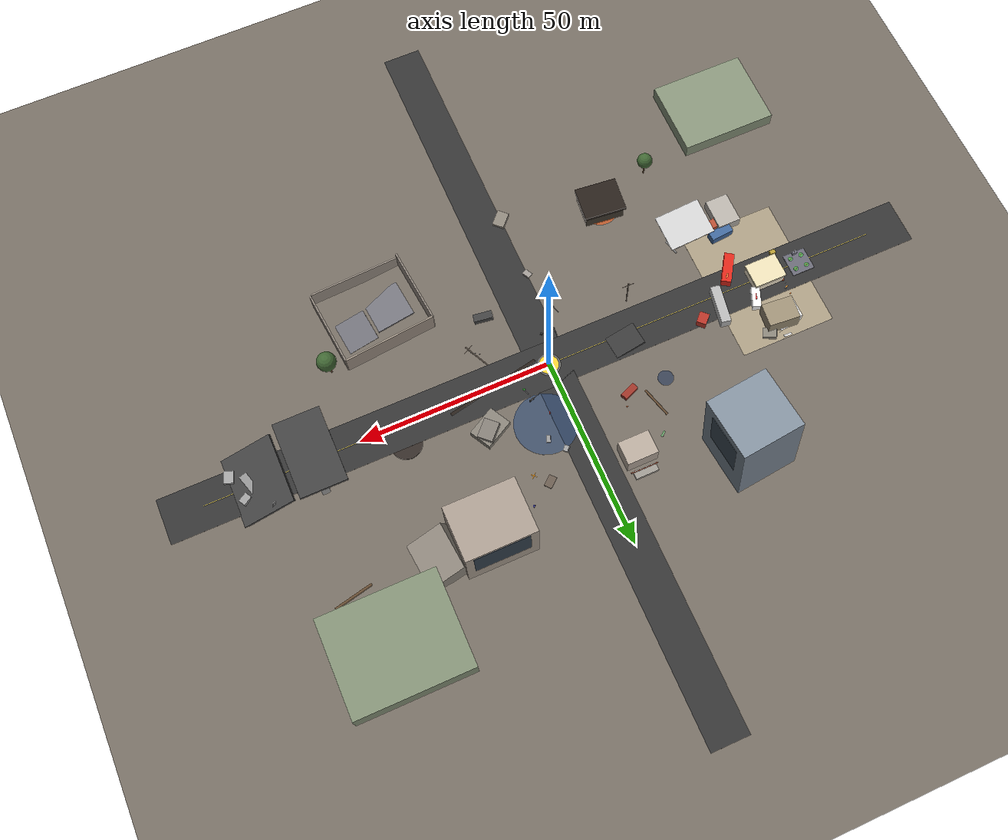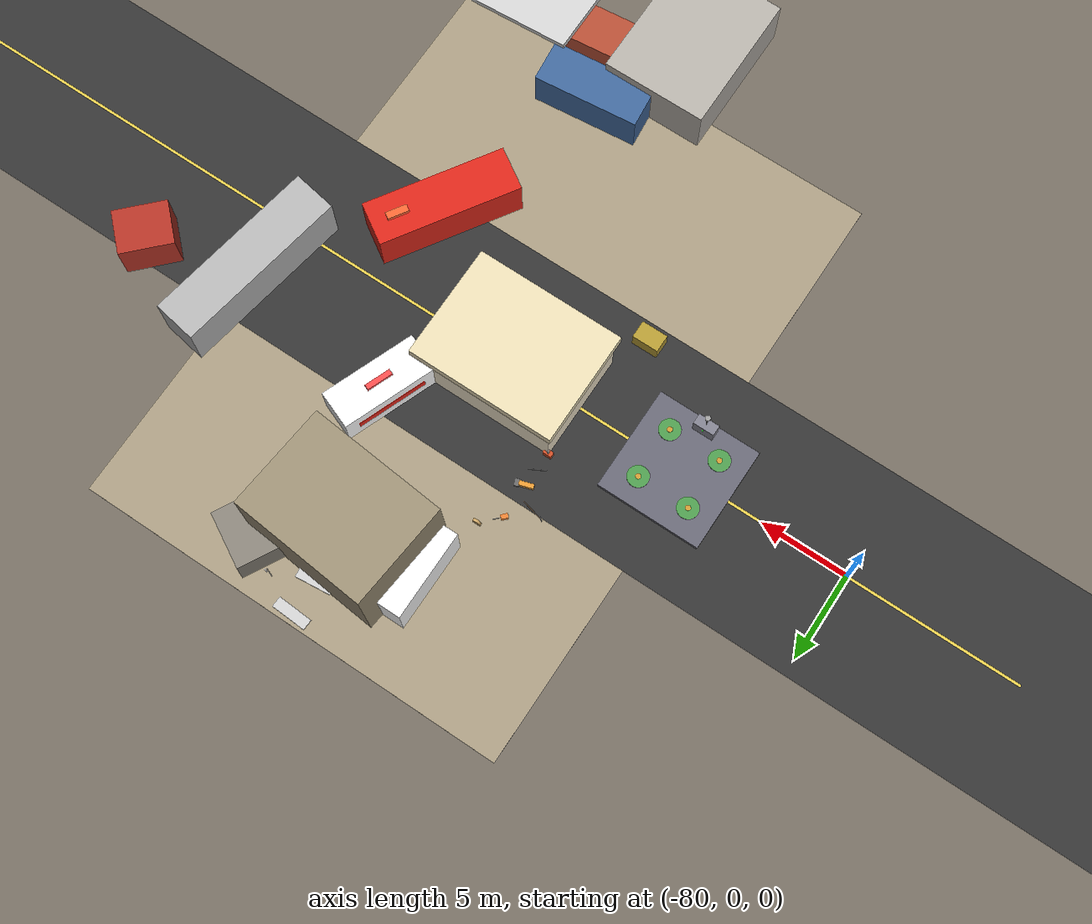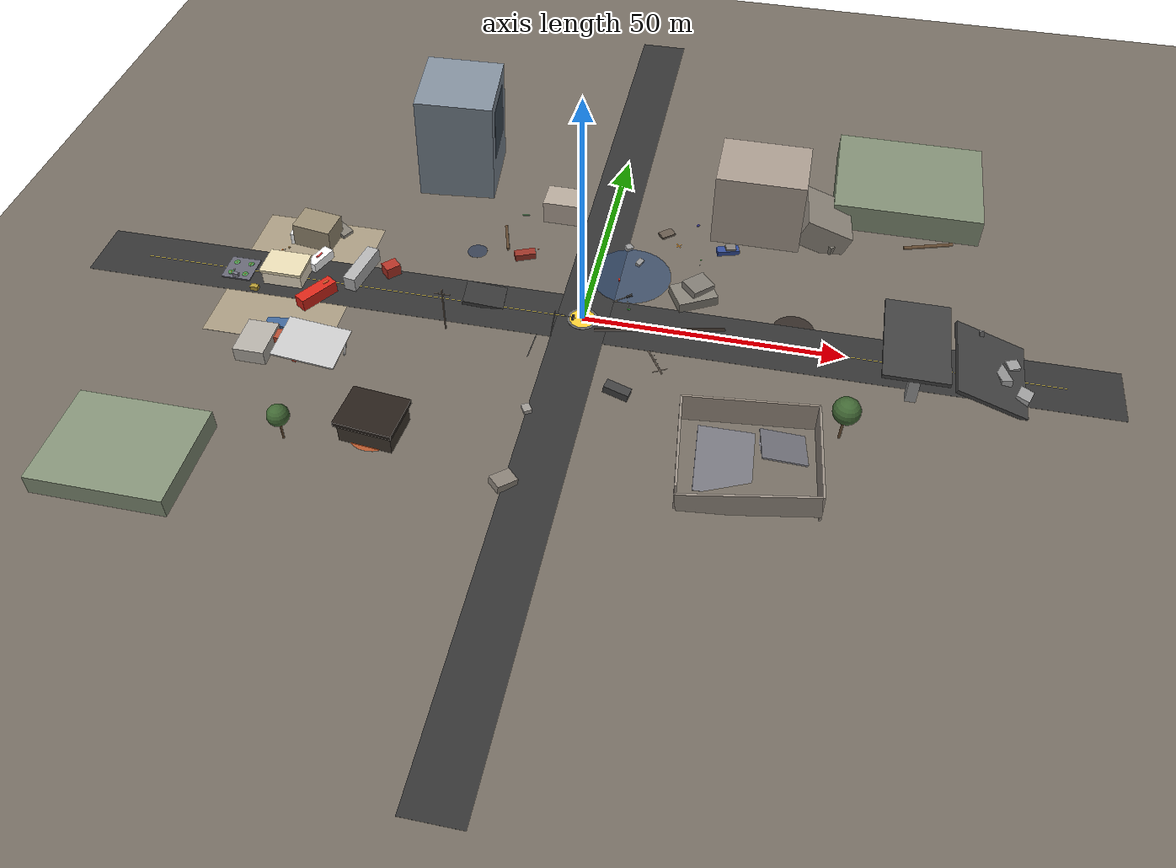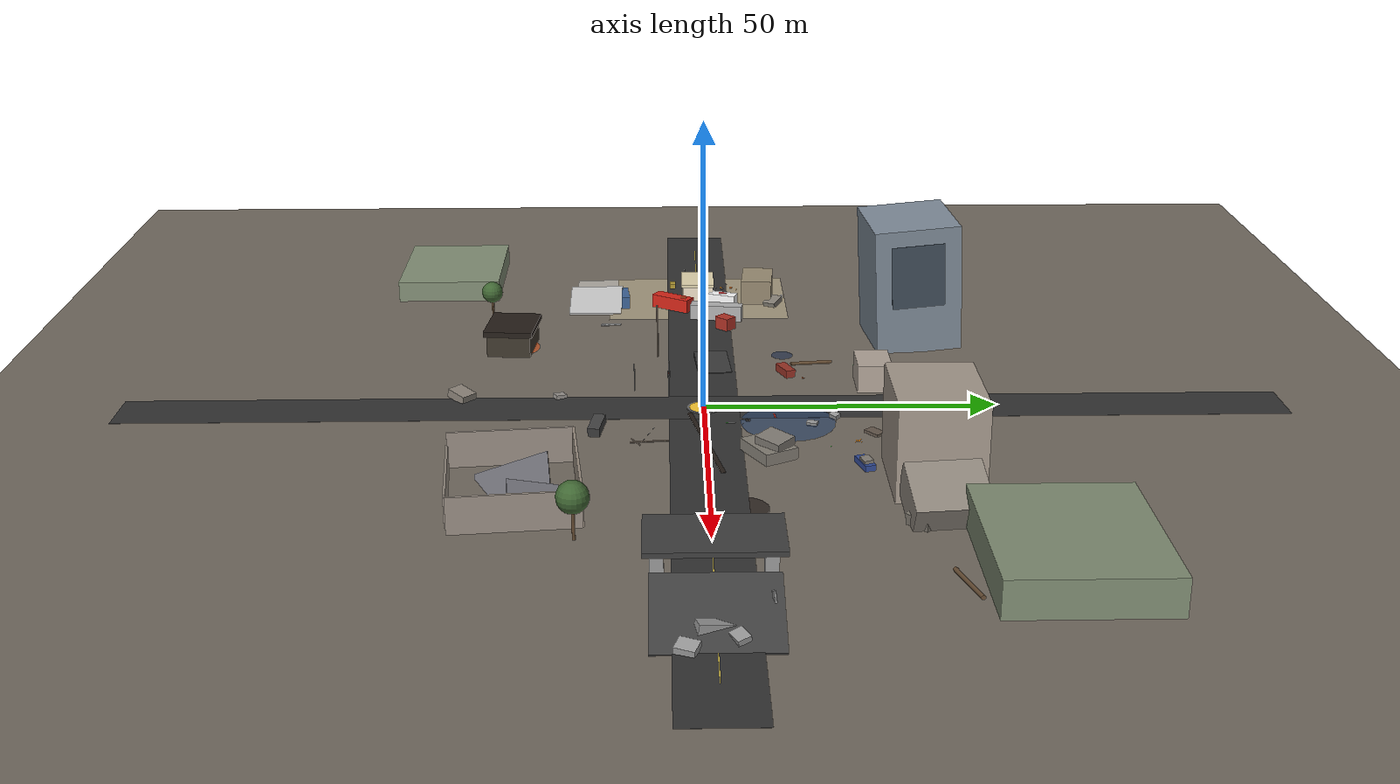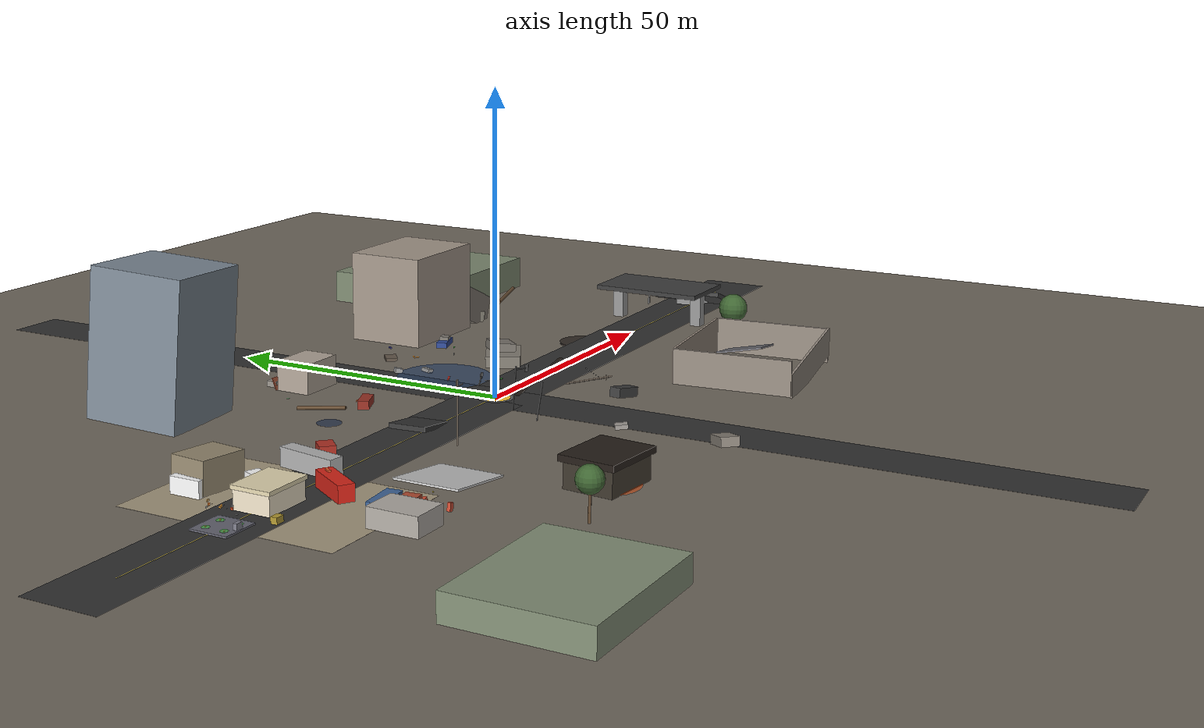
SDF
<sdf version="1.9">
 <world name="earthquake_zone">
  <physics name="1ms" type="ignored">
   <max_step_size>0.001</max_step_size>
   <real_time_factor>1.0</real_time_factor>
   <real_time_update_rate>1000</real_time_update_rate>
  </physics>
  <plugin filename="gz-sim-physics-system" name="gz::sim::systems::Physics"/>
  <plugin filename="gz-sim-user-commands-system" name="gz::sim::systems::UserCommands"/>
  <plugin filename="gz-sim-scene-broadcaster-system" name="gz::sim::systems::SceneBroadcaster"/>
  <plugin filename="gz-sim-sensors-system" name="gz::sim::systems::Sensors">
   <render_engine>ogre2</render_engine>
  </plugin>
  <plugin filename="gz-sim-imu-system" name="gz::sim::systems::Imu"/>
  <plugin filename="gz-sim-navsat-system" name="gz::sim::systems::NavSat"/>
  <plugin filename="gz-sim-contact-system" name="gz::sim::systems::Contact"/>
  <plugin filename="gz-sim-particle-emitter-system" name="gz::sim::systems::ParticleEmitter"/>
  <plugin filename="gz-sim-wind-effects-system" name="gz::sim::systems::WindEffects">
   <force_approximation_scaling_factor>1.0</force_approximation_scaling_factor>
   <horizontal>
    <magnitude>
     <time_for_rise>10</time_for_rise>
     <sin><amplitude_percent>0.3</amplitude_percent><period>60</period></sin>
     <noise type="gaussian"><mean>0</mean><stddev>0.5</stddev></noise>
    </magnitude>
    <direction>
     <time_for_rise>30</time_for_rise>
     <sin><amplitude>0.5</amplitude><period>120</period></sin>
     <noise type="gaussian"><mean>0</mean><stddev>0.1</stddev></noise>
    </direction>
   </horizontal>
   <vertical><noise type="gaussian"><mean>0</mean><stddev>0.2</stddev></noise></vertical>
  </plugin>
  <spherical_coordinates>
   <surface_model>EARTH_WGS84</surface_model>
   <world_frame_orientation>ENU</world_frame_orientation>
   <latitude_deg>37.7749</latitude_deg>
   <longitude_deg>-122.4194</longitude_deg>
   <elevation>0</elevation>
   <heading_deg>0</heading_deg>
  </spherical_coordinates>
  <scene>
   <ambient>0.5 0.5 0.5 1</ambient>
   <background>0.6 0.55 0.5 1</background>
   <shadows>true</shadows>
   <fog>
    <color>0.7 0.65 0.6 1</color>
    <type>linear</type>
    <start>50</start>
    <end>300</end>
    <density>0.02</density>
   </fog>
  </scene>
  <light type="directional" name="sun">
   <pose>0 0 100 0 0 0</pose>
   <diffuse>0.85 0.8 0.7 1</diffuse>
   <specular>0.2 0.2 0.2 1</specular>
   <attenuation>
    <range>1000</range>
    <constant>0.9</constant>
    <linear>0.01</linear>
    <quadratic>0.001</quadratic>
   </attenuation>
   <direction>-0.5 0.3 -0.9</direction>
  </light>
  <light type="directional" name="fill_light">
   <cast_shadows>false</cast_shadows>
   <pose>0 0 50 0 0 0</pose>
   <diffuse>0.3 0.3 0.35 1</diffuse>
   <specular>0.05 0.05 0.05 1</specular>
   <direction>0.5 -0.3 -0.5</direction>
  </light>
  <light type="point" name="fire_glow_1">
   <pose>-30 -35 3 0 0 0</pose>
   <diffuse>1.0 0.4 0.1 1</diffuse>
   <specular>0.3 0.1 0.0 1</specular>
   <attenuation>
    <range>15</range>
    <constant>0.5</constant>
    <linear>0.1</linear>
    <quadratic>0.02</quadratic>
   </attenuation>
  </light>
  <light type="point" name="ambulance_light_red">
   <pose>-55 5 2.5 0 0 0</pose>
   <diffuse>1.0 0.1 0.1 1</diffuse>
   <specular>0.5 0.0 0.0 1</specular>
   <attenuation>
    <range>10</range>
    <constant>0.5</constant>
    <linear>0.2</linear>
    <quadratic>0.05</quadratic>
   </attenuation>
  </light>
  <light type="point" name="firetruck_light_red">
   <pose>-52 -5 3 0 0 0</pose>
   <diffuse>1.0 0.2 0.0 1</diffuse>
   <specular>0.5 0.1 0.0 1</specular>
   <attenuation>
    <range>12</range>
    <constant>0.5</constant>
    <linear>0.15</linear>
    <quadratic>0.04</quadratic>
   </attenuation>
  </light>
  <light type="point" name="staging_light_1">
   <pose>-60 0 5 0 0 0</pose>
   <diffuse>0.9 0.9 0.8 1</diffuse>
   <specular>0.3 0.3 0.3 1</specular>
   <attenuation>
    <range>20</range>
    <constant>0.4</constant>
    <linear>0.1</linear>
    <quadratic>0.02</quadratic>
   </attenuation>
  </light>
  <light type="point" name="staging_light_2">
   <pose>-60 12 5 0 0 0</pose>
   <diffuse>0.9 0.9 0.8 1</diffuse>
   <specular>0.3 0.3 0.3 1</specular>
   <attenuation>
    <range>15</range>
    <constant>0.4</constant>
    <linear>0.1</linear>
    <quadratic>0.02</quadratic>
   </attenuation>
  </light>
  <model name="ground_plane">
   <static>true</static>
   <link name="link">
    <collision name="collision">
     <geometry><plane><normal>0 0 1</normal><size>300 300</size></plane></geometry>
     <surface><friction><ode><mu>100</mu><mu2>50</mu2></ode></friction></surface>
    </collision>
    <visual name="visual">
     <geometry><plane><normal>0 0 1</normal><size>300 300</size></plane></geometry>
     <material>
      <ambient>0.35 0.32 0.28 1</ambient>
      <diffuse>0.45 0.42 0.38 1</diffuse>
      <specular>0.05 0.05 0.05 1</specular>
     </material>
    </visual>
   </link>
  </model>
  <model name="main_road_ew">
   <static>true</static>
   <pose>0 0 0.02 0 0 0</pose>
   <link name="link">
    <visual name="asphalt">
     <geometry><box><size>200 12 0.02</size></box></geometry>
     <material><ambient>0.15 0.15 0.15 1</ambient><diffuse>0.2 0.2 0.2 1</diffuse></material>
    </visual>
    <visual name="center_line">
     <pose>0 0 0.01 0 0 0</pose>
     <geometry><box><size>180 0.15 0.01</size></box></geometry>
     <material><ambient>0.8 0.7 0.2 1</ambient><diffuse>0.9 0.8 0.3 1</diffuse></material>
    </visual>
   </link>
  </model>
  <model name="cross_road_ns">
   <static>true</static>
   <pose>0 0 0.02 0 0 1.5708</pose>
   <link name="link">
    <visual name="asphalt">
     <geometry><box><size>200 10 0.02</size></box></geometry>
     <material><ambient>0.15 0.15 0.15 1</ambient><diffuse>0.2 0.2 0.2 1</diffuse></material>
    </visual>
   </link>
  </model>
  <model name="road_crack_1">
   <static>true</static>
   <pose>15 0 0.03 0 0 0.2</pose>
   <link name="link">
    <visual name="crack">
     <geometry><box><size>25 0.8 0.15</size></box></geometry>
     <material><ambient>0.1 0.08 0.06 1</ambient><diffuse>0.15 0.12 0.1 1</diffuse></material>
    </visual>
   </link>
  </model>
  <model name="road_upheaval">
   <static>true</static>
   <pose>-20 2 0 0 0.15 0.1</pose>
   <link name="link">
    <collision name="col"><geometry><box><size>8 6 0.8</size></box></geometry></collision>
    <visual name="vis">
     <pose>0 0 0.4 0 0 0</pose>
     <geometry><box><size>8 6 0.8</size></box></geometry>
     <material><ambient>0.18 0.18 0.18 1</ambient><diffuse>0.22 0.22 0.22 1</diffuse></material>
    </visual>
   </link>
  </model>
  <model name="overpass_collapsed">
   <static>true</static>
   <pose>70 0 0 0 0 0</pose>
   <link name="pillar_1">
    <pose>-8 -8 3 0 0 0</pose>
    <collision name="col"><geometry><box><size>2 2 6</size></box></geometry></collision>
    <visual name="vis">
     <geometry><box><size>2 2 6</size></box></geometry>
     <material><ambient>0.5 0.5 0.5 1</ambient><diffuse>0.6 0.6 0.6 1</diffuse></material>
    </visual>
   </link>
   <link name="pillar_2">
    <pose>-8 8 3 0 0 0</pose>
    <collision name="col"><geometry><box><size>2 2 6</size></box></geometry></collision>
    <visual name="vis">
     <geometry><box><size>2 2 6</size></box></geometry>
     <material><ambient>0.5 0.5 0.5 1</ambient><diffuse>0.6 0.6 0.6 1</diffuse></material>
    </visual>
   </link>
   <link name="pillar_fallen">
    <pose>8 0 1 1.4 0 0.3</pose>
    <collision name="col"><geometry><box><size>2 2 6</size></box></geometry></collision>
    <visual name="vis">
     <geometry><box><size>2 2 6</size></box></geometry>
     <material><ambient>0.48 0.48 0.48 1</ambient><diffuse>0.58 0.58 0.58 1</diffuse></material>
    </visual>
   </link>
   <link name="deck_standing">
    <pose>-8 0 6.5 0 0 0</pose>
    <collision name="col"><geometry><box><size>12 20 0.8</size></box></geometry></collision>
    <visual name="vis">
     <geometry><box><size>12 20 0.8</size></box></geometry>
     <material><ambient>0.2 0.2 0.2 1</ambient><diffuse>0.25 0.25 0.25 1</diffuse></material>
    </visual>
   </link>
   <link name="deck_collapsed">
    <pose>6 0 2 0 0.35 0</pose>
    <collision name="col"><geometry><box><size>14 18 0.8</size></box></geometry></collision>
    <visual name="vis">
     <geometry><box><size>14 18 0.8</size></box></geometry>
     <material><ambient>0.2 0.2 0.2 1</ambient><diffuse>0.25 0.25 0.25 1</diffuse></material>
    </visual>
   </link>
   <link name="guardrail_1">
    <pose>5 8 0.5 0.2 1.3 0.5</pose>
    <collision name="col"><geometry><box><size>8 0.3 0.8</size></box></geometry></collision>
    <visual name="vis">
     <geometry><box><size>8 0.3 0.8</size></box></geometry>
     <material><ambient>0.4 0.4 0.4 1</ambient><diffuse>0.5 0.5 0.5 1</diffuse></material>
    </visual>
   </link>
   <link name="chunk_1">
    <pose>10 3 0 0.2 0.1 0.5</pose>
    <collision name="col"><geometry><box><size>2.5 2 1.5</size></box></geometry></collision>
    <visual name="vis">
     <pose>0 0 0.75 0 0 0</pose>
     <geometry><box><size>2.5 2 1.5</size></box></geometry>
     <material><ambient>0.5 0.5 0.5 1</ambient><diffuse>0.6 0.6 0.6 1</diffuse></material>
    </visual>
   </link>
   <link name="chunk_2">
    <pose>12 -4 0 0.15 0.05 1.2</pose>
    <collision name="col"><geometry><box><size>3 2.5 1.2</size></box></geometry></collision>
    <visual name="vis">
     <pose>0 0 0.6 0 0 0</pose>
     <geometry><box><size>3 2.5 1.2</size></box></geometry>
     <material><ambient>0.52 0.52 0.52 1</ambient><diffuse>0.62 0.62 0.62 1</diffuse></material>
    </visual>
   </link>
  </model>
  <model name="traffic_light_fallen">
   <static>true</static>
   <pose>5 6 0 0 1.3 0.4</pose>
   <link name="pole">
    <collision name="col">
     <geometry><cylinder><radius>0.1</radius><length>7</length></cylinder></geometry>
    </collision>
    <visual name="vis">
     <geometry><cylinder><radius>0.1</radius><length>7</length></cylinder></geometry>
     <material><ambient>0.25 0.25 0.25 1</ambient><diffuse>0.35 0.35 0.35 1</diffuse></material>
    </visual>
   </link>
   <link name="signal_box">
    <pose>0 0 3.2 0 0 0</pose>
    <collision name="col"><geometry><box><size>0.4 0.4 1.2</size></box></geometry></collision>
    <visual name="vis">
     <geometry><box><size>0.4 0.4 1.2</size></box></geometry>
     <material><ambient>0.15 0.15 0.15 1</ambient><diffuse>0.2 0.2 0.2 1</diffuse></material>
    </visual>
   </link>
  </model>
  <model name="traffic_light_tilted">
   <static>true</static>
   <pose>-5 -6 0 0 0.15 0</pose>
   <link name="pole">
    <pose>0 0 3.5 0 0 0</pose>
    <collision name="col">
     <geometry><cylinder><radius>0.1</radius><length>7</length></cylinder></geometry>
    </collision>
    <visual name="vis">
     <geometry><cylinder><radius>0.1</radius><length>7</length></cylinder></geometry>
     <material><ambient>0.25 0.25 0.25 1</ambient><diffuse>0.35 0.35 0.35 1</diffuse></material>
    </visual>
   </link>
   <link name="arm">
    <pose>2 0 6.5 0 1.57 0</pose>
    <visual name="vis">
     <geometry><cylinder><radius>0.08</radius><length>4</length></cylinder></geometry>
     <material><ambient>0.25 0.25 0.25 1</ambient><diffuse>0.35 0.35 0.35 1</diffuse></material>
    </visual>
   </link>
   <link name="signal_box">
    <pose>3.5 0 6.5 0 0 0</pose>
    <visual name="vis">
     <geometry><box><size>0.4 0.4 1.2</size></box></geometry>
     <material><ambient>0.15 0.15 0.15 1</ambient><diffuse>0.2 0.2 0.2 1</diffuse></material>
    </visual>
    <visual name="red_light">
     <pose>0.21 0 0.35 0 1.57 0</pose>
     <geometry><cylinder><radius>0.12</radius><length>0.05</length></cylinder></geometry>
     <material><ambient>0.3 0.1 0.1 1</ambient><diffuse>0.4 0.15 0.15 1</diffuse></material>
    </visual>
   </link>
  </model>
  <model name="apartment_collapsed">
   <static>true</static>
   <pose>30 35 0 0 0 0</pose>
   <link name="main_structure">
    <collision name="col">
     <pose>0 0 8 0 0 0</pose>
     <geometry><box><size>18 14 16</size></box></geometry>
    </collision>
    <visual name="facade">
     <pose>0 0 8 0 0 0</pose>
     <geometry><box><size>18 14 16</size></box></geometry>
     <material>
      <ambient>0.55 0.5 0.45 1</ambient>
      <diffuse>0.65 0.6 0.55 1</diffuse>
      <pbr><metal><roughness>0.8</roughness><metalness>0.1</metalness></metal></pbr>
      <specular>0.3 0.3 0.3 1</specular>
     </material>
    </visual>
    <visual name="windows_front">
     <pose>0 7.01 10 0 0 0</pose>
     <geometry><box><size>14 0.1 10</size></box></geometry>
     <material><ambient>0.15 0.2 0.25 1</ambient><diffuse>0.2 0.25 0.3 1</diffuse></material>
    </visual>
    <particle_emitter name="smoke_apartment" type="box">
     <pose>5 0 16 0 0 0</pose>
     <emitting>true</emitting>
     <size>4 4 1</size>
     <particle_size>3 3 3</particle_size>
     <lifetime>8</lifetime>
     <min_velocity>0.5</min_velocity>
     <max_velocity>2</max_velocity>
     <scale_rate>1.5</scale_rate>
     <rate>5</rate>
     <material><diffuse>0.5 0.5 0.5 0.3</diffuse></material>
     <color_range_image>https://fuel.gazebosim.org/1.0/openrobotics/models/smoke_generator/1/files/materials/textures/smoke.png</color_range_image>
    </particle_emitter>
   </link>
   <link name="collapsed_wing">
    <pose>12 0 0 0 0.4 0.1</pose>
    <collision name="col"><pose>0 0 3 0 0 0</pose><geometry><box><size>10 12 6</size></box></geometry></collision>
    <visual name="vis">
     <pose>0 0 3 0 0 0</pose>
     <geometry><box><size>10 12 6</size></box></geometry>
     <material>
      <ambient>0.45 0.42 0.38 1</ambient>
      <diffuse>0.55 0.52 0.48 1</diffuse>
      <pbr><metal><roughness>0.8</roughness><metalness>0.1</metalness></metal></pbr>
      <specular>0.3 0.3 0.3 1</specular>
     </material>
    </visual>
   </link>
   <link name="debris_1">
    <pose>18 5 0 0 0.2 0.5</pose>
    <collision name="col"><geometry><box><size>6 4 2.5</size></box></geometry></collision>
    <visual name="vis">
     <pose>0 0 1.25 0 0 0</pose>
     <geometry><box><size>6 4 2.5</size></box></geometry>
     <material>
      <ambient>0.4 0.38 0.35 1</ambient>
      <diffuse>0.5 0.48 0.45 1</diffuse>
      <pbr><metal><roughness>0.8</roughness><metalness>0.1</metalness></metal></pbr>
      <specular>0.3 0.3 0.3 1</specular>
     </material>
    </visual>
   </link>
   <link name="debris_2">
    <pose>15 -3 0 0.15 0 0.8</pose>
    <collision name="col"><geometry><box><size>4 5 2</size></box></geometry></collision>
    <visual name="vis">
     <pose>0 0 1 0 0 0</pose>
     <geometry><box><size>4 5 2</size></box></geometry>
     <material>
      <ambient>0.38 0.36 0.32 1</ambient>
      <diffuse>0.48 0.46 0.42 1</diffuse>
      <pbr><metal><roughness>0.8</roughness><metalness>0.1</metalness></metal></pbr>
      <specular>0.3 0.3 0.3 1</specular>
     </material>
    </visual>
   </link>
  </model>
  <model name="dust_cloud_apartment">
   <static>true</static>
   <pose>42 35 1 0 0 0</pose>
   <link name="link">
    <particle_emitter name="dust_emitter" type="box">
     <emitting>true</emitting>
     <size>8 8 2</size>
     <particle_size>4 4 4</particle_size>
     <lifetime>12</lifetime>
     <min_velocity>0.1</min_velocity>
     <max_velocity>0.5</max_velocity>
     <scale_rate>0.8</scale_rate>
     <rate>2</rate>
     <material><diffuse>0.6 0.55 0.5 0.15</diffuse></material>
    </particle_emitter>
   </link>
  </model>
  <model name="office_tower">
   <static>true</static>
   <pose>-35 40 0 0.06 0.04 0.1</pose>
   <link name="tower">
    <collision name="col">
     <pose>0 0 12 0 0 0</pose>
     <geometry><box><size>16 16 24</size></box></geometry>
    </collision>
    <visual name="main">
     <pose>0 0 12 0 0 0</pose>
     <geometry><box><size>16 16 24</size></box></geometry>
     <material>
      <ambient>0.4 0.45 0.5 1</ambient>
      <diffuse>0.5 0.55 0.6 1</diffuse>
      <pbr><metal><roughness>0.6</roughness><metalness>0.2</metalness></metal></pbr>
      <specular>0.3 0.3 0.3 1</specular>
     </material>
    </visual>
    <visual name="glass_damage">
     <pose>8.01 0 15 0 0 0</pose>
     <geometry><box><size>0.1 10 12</size></box></geometry>
     <material>
      <ambient>0.2 0.25 0.3 1</ambient>
      <diffuse>0.25 0.3 0.35 1</diffuse>
      <specular>0.9 0.9 0.9 1</specular>
     </material>
    </visual>
   </link>
  </model>
  <model name="shop_collapsed">
   <static>true</static>
   <pose>-10 30 0 0 0 0</pose>
   <link name="structure">
    <collision name="col"><pose>0 0 2.5 0 0 0</pose><geometry><box><size>8 6 5</size></box></geometry></collision>
    <visual name="walls">
     <pose>0 0 2.5 0 0 0</pose>
     <geometry><box><size>8 6 5</size></box></geometry>
     <material>
      <ambient>0.6 0.55 0.5 1</ambient>
      <diffuse>0.7 0.65 0.6 1</diffuse>
      <pbr><metal><roughness>0.8</roughness><metalness>0.1</metalness></metal></pbr>
      <specular>0.3 0.3 0.3 1</specular>
     </material>
    </visual>
   </link>
   <link name="awning">
    <pose>0 4 0.3 1.2 0 0</pose>
    <visual name="vis">
     <geometry><box><size>7 3 0.1</size></box></geometry>
     <material>
      <ambient>0.5 0.2 0.15 1</ambient>
      <diffuse>0.6 0.3 0.2 1</diffuse>
      <pbr><metal><roughness>0.8</roughness><metalness>0.1</metalness></metal></pbr>
      <specular>0.3 0.3 0.3 1</specular>
     </material>
    </visual>
   </link>
   <link name="facade_debris">
    <pose>0 5 0 0 0 0</pose>
    <collision name="col"><geometry><box><size>6 2 1</size></box></geometry></collision>
    <visual name="vis">
     <pose>0 0 0.5 0 0 0</pose>
     <geometry><box><size>6 2 1</size></box></geometry>
     <material>
      <ambient>0.5 0.48 0.45 1</ambient>
      <diffuse>0.6 0.58 0.55 1</diffuse>
      <pbr><metal><roughness>0.8</roughness><metalness>0.1</metalness></metal></pbr>
      <specular>0.3 0.3 0.3 1</specular>
     </material>
    </visual>
   </link>
  </model>
  <model name="warehouse">
   <static>true</static>
   <pose>35 -30 0 0 0 0.1</pose>
   <link name="wall_north">
    <pose>0 10 3 0 0 0</pose>
    <collision name="col"><geometry><box><size>24 0.4 6</size></box></geometry></collision>
    <visual name="vis">
     <geometry><box><size>24 0.4 6</size></box></geometry>
     <material>
      <ambient>0.5 0.45 0.4 1</ambient>
      <diffuse>0.6 0.55 0.5 1</diffuse>
      <pbr><metal><roughness>0.9</roughness><metalness>0.15</metalness></metal></pbr>
      <specular>0.3 0.3 0.3 1</specular>
     </material>
    </visual>
   </link>
   <link name="wall_south">
    <pose>0 -10 2.5 0 -0.1 0</pose>
    <collision name="col"><geometry><box><size>24 0.4 5</size></box></geometry></collision>
    <visual name="vis">
     <geometry><box><size>24 0.4 5</size></box></geometry>
     <material>
      <ambient>0.48 0.44 0.4 1</ambient>
      <diffuse>0.58 0.54 0.5 1</diffuse>
      <pbr><metal><roughness>0.9</roughness><metalness>0.15</metalness></metal></pbr>
      <specular>0.3 0.3 0.3 1</specular>
     </material>
    </visual>
   </link>
   <link name="wall_east">
    <pose>12 0 3 0 0 0</pose>
    <collision name="col"><geometry><box><size>0.4 20 6</size></box></geometry></collision>
    <visual name="vis">
     <geometry><box><size>0.4 20 6</size></box></geometry>
     <material>
      <ambient>0.5 0.46 0.42 1</ambient>
      <diffuse>0.6 0.56 0.52 1</diffuse>
      <pbr><metal><roughness>0.9</roughness><metalness>0.15</metalness></metal></pbr>
      <specular>0.3 0.3 0.3 1</specular>
     </material>
    </visual>
   </link>
   <link name="wall_west">
    <pose>-12 0 3 0 0 0</pose>
    <collision name="col"><geometry><box><size>0.4 20 6</size></box></geometry></collision>
    <visual name="vis">
     <geometry><box><size>0.4 20 6</size></box></geometry>
     <material>
      <ambient>0.5 0.46 0.42 1</ambient>
      <diffuse>0.6 0.56 0.52 1</diffuse>
      <pbr><metal><roughness>0.9</roughness><metalness>0.15</metalness></metal></pbr>
      <specular>0.3 0.3 0.3 1</specular>
     </material>
    </visual>
   </link>
   <link name="roof_collapsed_1">
    <pose>-4 0 1 0.3 0.1 0</pose>
    <collision name="col"><geometry><box><size>10 12 0.3</size></box></geometry></collision>
    <visual name="vis">
     <geometry><box><size>10 12 0.3</size></box></geometry>
     <material>
      <ambient>0.35 0.35 0.38 1</ambient>
      <diffuse>0.45 0.45 0.48 1</diffuse>
      <pbr><metal><roughness>0.9</roughness><metalness>0.15</metalness></metal></pbr>
      <specular>0.3 0.3 0.3 1</specular>
     </material>
    </visual>
   </link>
   <link name="roof_collapsed_2">
    <pose>6 3 2.5 -0.2 0.15 0</pose>
    <collision name="col"><geometry><box><size>8 8 0.3</size></box></geometry></collision>
    <visual name="vis">
     <geometry><box><size>8 8 0.3</size></box></geometry>
     <material>
      <ambient>0.35 0.35 0.38 1</ambient>
      <diffuse>0.45 0.45 0.48 1</diffuse>
      <pbr><metal><roughness>0.9</roughness><metalness>0.15</metalness></metal></pbr>
      <specular>0.3 0.3 0.3 1</specular>
     </material>
    </visual>
   </link>
  </model>
  <model name="house_burned">
   <static>true</static>
   <pose>-30 -35 0 0 0 -0.1</pose>
   <link name="structure">
    <collision name="col"><pose>0 0 2 0 0 0</pose><geometry><box><size>10 8 4</size></box></geometry></collision>
    <visual name="walls">
     <pose>0 0 2 0 0 0</pose>
     <geometry><box><size>10 8 4</size></box></geometry>
     <material>
      <ambient>0.2 0.18 0.15 1</ambient>
      <diffuse>0.25 0.22 0.18 1</diffuse>
      <pbr><metal><roughness>0.95</roughness><metalness>0.0</metalness></metal></pbr>
      <specular>0.3 0.3 0.3 1</specular>
     </material>
    </visual>
    <visual name="roof">
     <pose>0 0 4.5 0 0 0</pose>
     <geometry><box><size>11 9 1</size></box></geometry>
     <material>
      <ambient>0.1 0.08 0.06 1</ambient>
      <diffuse>0.15 0.12 0.1 1</diffuse>
      <pbr><metal><roughness>0.95</roughness><metalness>0.0</metalness></metal></pbr>
      <specular>0.3 0.3 0.3 1</specular>
     </material>
    </visual>
    <particle_emitter name="fire_house" type="box">
     <pose>2 0 4 0 0 0</pose>
     <emitting>true</emitting>
     <size>3 3 0.5</size>
     <particle_size>1.5 1.5 2</particle_size>
     <lifetime>2</lifetime>
     <min_velocity>1</min_velocity>
     <max_velocity>3</max_velocity>
     <scale_rate>0.5</scale_rate>
     <rate>15</rate>
     <material><diffuse>1.0 0.5 0.1 0.8</diffuse></material>
    </particle_emitter>
    <particle_emitter name="smoke_house" type="box">
     <pose>2 0 6 0 0 0</pose>
     <emitting>true</emitting>
     <size>4 4 1</size>
     <particle_size>4 4 4</particle_size>
     <lifetime>10</lifetime>
     <min_velocity>1</min_velocity>
     <max_velocity>3</max_velocity>
     <scale_rate>2</scale_rate>
     <rate>8</rate>
     <material><diffuse>0.3 0.3 0.3 0.4</diffuse></material>
    </particle_emitter>
   </link>
  </model>
  <model name="heat_source_1">
   <static>true</static>
   <pose>-30 -35 0.1 0 0 0</pose>
   <link name="link">
    <visual name="heat_marker">
     <geometry><cylinder><radius>5</radius><length>0.05</length></cylinder></geometry>
     <material>
      <ambient>0.8 0.2 0.0 0.5</ambient>
      <diffuse>1.0 0.3 0.0 0.5</diffuse>
      <emissive>1.0 0.3 0.0 1</emissive>
     </material>
    </visual>
   </link>
  </model>
  <model name="gas_station">
   <static>true</static>
   <pose>-50 -20 0 0 0 0</pose>
   <link name="building">
    <collision name="col">
     <pose>-8 0 1.5 0 0 0</pose>
     <geometry><box><size>6 8 3</size></box></geometry>
    </collision>
    <visual name="vis">
     <pose>-8 0 1.5 0 0 0</pose>
     <geometry><box><size>6 8 3</size></box></geometry>
     <material>
      <ambient>0.6 0.58 0.55 1</ambient>
      <diffuse>0.7 0.68 0.65 1</diffuse>
      <pbr><metal><roughness>0.7</roughness><metalness>0.1</metalness></metal></pbr>
      <specular>0.3 0.3 0.3 1</specular>
     </material>
    </visual>
   </link>
   <link name="canopy">
    <pose>3 0 3.5 0 0.12 0</pose>
    <collision name="col"><geometry><box><size>12 10 0.3</size></box></geometry></collision>
    <visual name="vis">
     <geometry><box><size>12 10 0.3</size></box></geometry>
     <material>
      <ambient>0.7 0.7 0.7 1</ambient>
      <diffuse>0.8 0.8 0.8 1</diffuse>
      <pbr><metal><roughness>0.7</roughness><metalness>0.1</metalness></metal></pbr>
      <specular>0.3 0.3 0.3 1</specular>
     </material>
    </visual>
   </link>
   <link name="pillar_fallen">
    <pose>8 3 0.2 1.5 0 0.3</pose>
    <collision name="col">
     <geometry><cylinder><radius>0.2</radius><length>4</length></cylinder></geometry>
    </collision>
    <visual name="vis">
     <geometry><cylinder><radius>0.2</radius><length>4</length></cylinder></geometry>
     <material>
      <ambient>0.5 0.5 0.5 1</ambient>
      <diffuse>0.6 0.6 0.6 1</diffuse>
      <pbr><metal><roughness>0.7</roughness><metalness>0.1</metalness></metal></pbr>
      <specular>0.3 0.3 0.3 1</specular>
     </material>
    </visual>
   </link>
   <link name="pump_1">
    <pose>0 -2 0.6 0 0.2 0</pose>
    <visual name="vis">
     <geometry><box><size>0.8 0.5 1.2</size></box></geometry>
     <material>
      <ambient>0.7 0.2 0.15 1</ambient>
      <diffuse>0.8 0.3 0.2 1</diffuse>
      <pbr><metal><roughness>0.7</roughness><metalness>0.1</metalness></metal></pbr>
      <specular>0.3 0.3 0.3 1</specular>
     </material>
    </visual>
   </link>
   <link name="pump_2">
    <pose>0 2 0.6 0 -0.15 0</pose>
    <visual name="vis">
     <geometry><box><size>0.8 0.5 1.2</size></box></geometry>
     <material>
      <ambient>0.7 0.2 0.15 1</ambient>
      <diffuse>0.8 0.3 0.2 1</diffuse>
      <pbr><metal><roughness>0.7</roughness><metalness>0.1</metalness></metal></pbr>
      <specular>0.3 0.3 0.3 1</specular>
     </material>
    </visual>
   </link>
   <link name="gas_leak">
    <pose>2 0 0.5 0 0 0</pose>
    <particle_emitter name="gas_leak_smoke" type="point">
     <emitting>true</emitting>
     <size>0.5 0.5 0.5</size>
     <particle_size>1 1 1</particle_size>
     <lifetime>4</lifetime>
     <min_velocity>0.3</min_velocity>
     <max_velocity>1</max_velocity>
     <scale_rate>0.5</scale_rate>
     <rate>3</rate>
     <material><diffuse>0.7 0.7 0.5 0.2</diffuse></material>
    </particle_emitter>
   </link>
  </model>
  <model name="shop_damaged">
   <static>true</static>
   <pose>-58 12 0 0 0.04 -0.1</pose>
   <link name="structure">
    <collision name="col"><geometry><box><size>8 6 5</size></box></geometry><pose>0 0 2.5 0 0 0</pose></collision>
    <visual name="facade">
     <pose>0 0 2.5 0 0 0</pose>
     <geometry><box><size>8 6 5</size></box></geometry>
     <material>
      <ambient>0.6 0.55 0.45 1</ambient>
      <diffuse>0.6 0.55 0.45 1</diffuse>
      <specular>0.2 0.2 0.2 1</specular>
      <pbr><metal><roughness>0.85</roughness><metalness>0.05</metalness></metal></pbr>
     </material>
    </visual>
   </link>
  </model>
  <model name="rubble_debris_1">
   <static>true</static>
   <pose>-5 -42 0 0 0.15 0.8</pose>
   <link name="debris">
    <collision name="col"><geometry><box><size>4 3 1.5</size></box></geometry></collision>
    <visual name="vis">
     <pose>0 0 0.75 0 0 0</pose>
     <geometry><box><size>4 3 1.5</size></box></geometry>
     <material>
      <ambient>0.45 0.42 0.38 1</ambient>
      <diffuse>0.55 0.52 0.48 1</diffuse>
      <specular>0.3 0.3 0.3 1</specular>
      <pbr><metal><roughness>0.9</roughness><metalness>0.05</metalness></metal></pbr>
     </material>
    </visual>
   </link>
  </model>
  <model name="rubble_debris_2">
   <static>true</static>
   <pose>-54 15 0 0 0.2 -0.5</pose>
   <link name="debris">
    <collision name="col"><geometry><box><size>3.5 2.5 1.2</size></box></geometry></collision>
    <visual name="vis">
     <pose>0 0 0.6 0 0 0</pose>
     <geometry><box><size>3.5 2.5 1.2</size></box></geometry>
     <material>
      <ambient>0.42 0.40 0.36 1</ambient>
      <diffuse>0.52 0.50 0.46 1</diffuse>
      <specular>0.3 0.3 0.3 1</specular>
      <pbr><metal><roughness>0.9</roughness><metalness>0.05</metalness></metal></pbr>
     </material>
    </visual>
   </link>
  </model>
  <model name="victim_2">
   <static>true</static>
   <pose>32 -28 0.5 1.4 0.3 0</pose>
   <link name="body">
    <visual name="torso">
     <geometry><box><size>0.5 0.3 0.8</size></box></geometry>
     <material><ambient>0.2 0.3 0.6 1</ambient><diffuse>0.3 0.4 0.7 1</diffuse></material>
    </visual>
    <visual name="head">
     <pose>0 0 0.55 0 0 0</pose>
     <geometry><sphere><radius>0.12</radius></sphere></geometry>
     <material><ambient>0.8 0.65 0.5 1</ambient><diffuse>0.9 0.75 0.6 1</diffuse></material>
    </visual>
    <visual name="aruco_marker">
     <pose>0 0.16 0 0 0 0</pose>
     <geometry><box><size>0.2 0.01 0.2</size></box></geometry>
     <material><ambient>0.9 0.9 0.9 1</ambient><diffuse>1 1 1 1</diffuse></material>
    </visual>
    <visual name="marker_pattern_2">
     <pose>0.04 0.165 0.04 0 0 0</pose>
     <geometry><box><size>0.06 0.005 0.06</size></box></geometry>
     <material><ambient>0.1 0.1 0.1 1</ambient><diffuse>0.15 0.15 0.15 1</diffuse></material>
    </visual>
   </link>
  </model>
  <model name="victim_5">
   <static>true</static>
   <pose>-8 34 0.15 1.57 0.1 1.2</pose>
   <link name="body">
    <visual name="torso">
     <geometry><box><size>0.5 0.3 0.8</size></box></geometry>
     <material><ambient>0.6 0.2 0.2 1</ambient><diffuse>0.7 0.3 0.3 1</diffuse></material>
    </visual>
    <visual name="head">
     <pose>0 0 0.55 0 0 0</pose>
     <geometry><sphere><radius>0.12</radius></sphere></geometry>
     <material><ambient>0.8 0.65 0.5 1</ambient><diffuse>0.9 0.75 0.6 1</diffuse></material>
    </visual>
    <visual name="aruco_marker">
     <pose>0 0.16 0 0 0 0</pose>
     <geometry><box><size>0.2 0.01 0.2</size></box></geometry>
     <material><ambient>0.9 0.9 0.9 1</ambient><diffuse>1 1 1 1</diffuse></material>
    </visual>
   </link>
  </model>
  <model name="search_flag_1">
   <static>true</static>
   <pose>20 20 0 0 0 0</pose>
   <link name="pole">
    <visual name="vis">
     <pose>0 0 0.75 0 0 0</pose>
     <geometry><cylinder><radius>0.02</radius><length>1.5</length></cylinder></geometry>
     <material><ambient>0.5 0.5 0.5 1</ambient><diffuse>0.6 0.6 0.6 1</diffuse></material>
    </visual>
   </link>
   <link name="flag">
    <pose>0.15 0 1.35 0 0 0</pose>
    <visual name="vis">
     <geometry><box><size>0.3 0.02 0.2</size></box></geometry>
     <material><ambient>0.1 0.7 0.1 1</ambient><diffuse>0.2 0.8 0.2 1</diffuse></material>
    </visual>
   </link>
  </model>
  <model name="search_flag_2">
   <static>true</static>
   <pose>44 36 0 0 0 0</pose>
   <link name="pole">
    <visual name="vis">
     <pose>0 0 0.75 0 0 0</pose>
     <geometry><cylinder><radius>0.02</radius><length>1.5</length></cylinder></geometry>
     <material><ambient>0.5 0.5 0.5 1</ambient><diffuse>0.6 0.6 0.6 1</diffuse></material>
    </visual>
   </link>
   <link name="flag">
    <pose>0.15 0 1.35 0 0 0</pose>
    <visual name="vis">
     <geometry><box><size>0.3 0.02 0.2</size></box></geometry>
     <material><ambient>0.8 0.1 0.1 1</ambient><diffuse>0.9 0.2 0.2 1</diffuse></material>
    </visual>
   </link>
  </model>
  <model name="search_flag_3">
   <static>true</static>
   <pose>-48 -18 0 0 0 0</pose>
   <link name="pole">
    <visual name="vis">
     <pose>0 0 0.75 0 0 0</pose>
     <geometry><cylinder><radius>0.02</radius><length>1.5</length></cylinder></geometry>
     <material><ambient>0.5 0.5 0.5 1</ambient><diffuse>0.6 0.6 0.6 1</diffuse></material>
    </visual>
   </link>
   <link name="flag">
    <pose>0.15 0 1.35 0 0 0</pose>
    <visual name="vis">
     <geometry><box><size>0.3 0.02 0.2</size></box></geometry>
     <material><ambient>0.9 0.8 0.1 1</ambient><diffuse>1.0 0.9 0.2 1</diffuse></material>
    </visual>
   </link>
  </model>
  <model name="spray_marker_1">
   <static>true</static>
   <pose>15 25 0.02 0 0 0.785</pose>
   <link name="link">
    <visual name="line1">
     <geometry><box><size>1.5 0.15 0.01</size></box></geometry>
     <material><ambient>0.9 0.5 0.0 1</ambient><diffuse>1.0 0.6 0.1 1</diffuse></material>
    </visual>
    <visual name="line2">
     <pose>0 0 0 0 0 1.57</pose>
     <geometry><box><size>1.5 0.15 0.01</size></box></geometry>
     <material><ambient>0.9 0.5 0.0 1</ambient><diffuse>1.0 0.6 0.1 1</diffuse></material>
    </visual>
   </link>
  </model>
  <model name="car_crushed">
   <static>true</static>
   <pose>25 25 0 0 0 0.3</pose>
   <link name="body">
    <collision name="col">
     <pose>0 0 0.5 0 0 0</pose>
     <geometry><box><size>4.5 1.8 1</size></box></geometry>
    </collision>
    <visual name="vis">
     <pose>0 0 0.5 0 0 0</pose>
     <geometry><box><size>4.5 1.8 1</size></box></geometry>
     <material><ambient>0.15 0.25 0.5 1</ambient><diffuse>0.2 0.3 0.6 1</diffuse></material>
    </visual>
   </link>
   <link name="debris">
    <pose>0.5 0 1.2 0.1 0.05 0</pose>
    <collision name="col"><geometry><box><size>2 1.5 0.8</size></box></geometry></collision>
    <visual name="vis">
     <geometry><box><size>2 1.5 0.8</size></box></geometry>
     <material><ambient>0.4 0.38 0.35 1</ambient><diffuse>0.5 0.48 0.45 1</diffuse></material>
    </visual>
   </link>
  </model>
  <model name="car_overturned">
   <static>true</static>
   <pose>-15 15 0.9 3.14 0 0.4</pose>
   <link name="body">
    <collision name="col"><geometry><box><size>4.2 1.8 1.4</size></box></geometry></collision>
    <visual name="vis">
     <geometry><box><size>4.2 1.8 1.4</size></box></geometry>
     <material><ambient>0.5 0.15 0.1 1</ambient><diffuse>0.6 0.2 0.15 1</diffuse></material>
    </visual>
   </link>
  </model>
  <model name="suv_damaged">
   <static>true</static>
   <pose>10 -18 0.3 0 0.15 -0.2</pose>
   <link name="body">
    <collision name="col">
     <pose>0 0 0.8 0 0 0</pose>
     <geometry><box><size>4.8 2 1.6</size></box></geometry>
    </collision>
    <visual name="vis">
     <pose>0 0 0.8 0 0 0</pose>
     <geometry><box><size>4.8 2 1.6</size></box></geometry>
     <material><ambient>0.2 0.2 0.2 1</ambient><diffuse>0.25 0.25 0.25 1</diffuse></material>
    </visual>
   </link>
  </model>
  <model name="truck_jackknifed">
   <static>true</static>
   <pose>-40 5 0 0 0 0.8</pose>
   <link name="cab">
    <collision name="col">
     <pose>0 0 1.2 0 0 0</pose>
     <geometry><box><size>3 2.5 2.4</size></box></geometry>
    </collision>
    <visual name="vis">
     <pose>0 0 1.2 0 0 0</pose>
     <geometry><box><size>3 2.5 2.4</size></box></geometry>
     <material><ambient>0.6 0.15 0.1 1</ambient><diffuse>0.7 0.2 0.15 1</diffuse></material>
    </visual>
   </link>
   <link name="trailer">
    <pose>-5 3 0 0 0 0.6</pose>
    <collision name="col">
     <pose>0 0 1.5 0 0 0</pose>
     <geometry><box><size>10 2.5 3</size></box></geometry>
    </collision>
    <visual name="vis">
     <pose>0 0 1.5 0 0 0</pose>
     <geometry><box><size>10 2.5 3</size></box></geometry>
     <material><ambient>0.6 0.6 0.6 1</ambient><diffuse>0.7 0.7 0.7 1</diffuse></material>
    </visual>
   </link>
  </model>
  <model name="ambulance">
   <static>true</static>
   <pose>-55 5 0 0 0 1.2</pose>
   <link name="body">
    <collision name="col">
     <pose>0 0 1 0 0 0</pose>
     <geometry><box><size>5.5 2.2 2</size></box></geometry>
    </collision>
    <visual name="body">
     <pose>0 0 1 0 0 0</pose>
     <geometry><box><size>5.5 2.2 2</size></box></geometry>
     <material><ambient>0.9 0.9 0.9 1</ambient><diffuse>1 1 1 1</diffuse></material>
    </visual>
    <visual name="stripe">
     <pose>0 1.11 1 0 0 0</pose>
     <geometry><box><size>4 0.02 0.5</size></box></geometry>
     <material><ambient>0.8 0.1 0.05 1</ambient><diffuse>0.9 0.15 0.1 1</diffuse></material>
    </visual>
    <visual name="lightbar">
     <pose>0 0 2.1 0 0 0</pose>
     <geometry><box><size>1.5 0.3 0.2</size></box></geometry>
     <material>
      <ambient>0.8 0.2 0.2 1</ambient>
      <diffuse>1.0 0.3 0.3 1</diffuse>
      <emissive>1.0 0.2 0.2 1</emissive>
     </material>
    </visual>
   </link>
  </model>
  <model name="fire_truck">
   <static>true</static>
   <pose>-52 -5 0 0 0 1.0</pose>
   <link name="body">
    <collision name="col">
     <pose>0 0 1.3 0 0 0</pose>
     <geometry><box><size>8 2.5 2.6</size></box></geometry>
    </collision>
    <visual name="vis">
     <pose>0 0 1.3 0 0 0</pose>
     <geometry><box><size>8 2.5 2.6</size></box></geometry>
     <material><ambient>0.7 0.1 0.05 1</ambient><diffuse>0.85 0.15 0.1 1</diffuse></material>
    </visual>
    <visual name="lightbar">
     <pose>2.5 0 2.7 0 0 0</pose>
     <geometry><box><size>1.2 0.4 0.25</size></box></geometry>
     <material>
      <ambient>0.9 0.3 0.1 1</ambient>
      <diffuse>1.0 0.4 0.2 1</diffuse>
      <emissive>1.0 0.3 0.1 1</emissive>
     </material>
    </visual>
   </link>
  </model>
  <model name="rubble_large_1">
   <static>true</static>
   <pose>20 10 0 0 0 0.5</pose>
   <link name="base">
    <collision name="col"><geometry><box><size>8 6 2</size></box></geometry></collision>
    <visual name="vis">
     <pose>0 0 1 0 0 0</pose>
     <geometry><box><size>8 6 2</size></box></geometry>
     <material><ambient>0.42 0.4 0.36 1</ambient><diffuse>0.52 0.5 0.46 1</diffuse></material>
    </visual>
   </link>
   <link name="top">
    <pose>1 0.5 2 0.1 0.05 0.3</pose>
    <collision name="col"><geometry><box><size>5 4 1.5</size></box></geometry></collision>
    <visual name="vis">
     <pose>0 0 0.75 0 0 0</pose>
     <geometry><box><size>5 4 1.5</size></box></geometry>
     <material><ambient>0.4 0.38 0.35 1</ambient><diffuse>0.5 0.48 0.45 1</diffuse></material>
    </visual>
   </link>
  </model>
  <model name="concrete_chunk_1">
   <static>true</static>
   <pose>5 22 0 0.2 0.1 0.8</pose>
   <link name="link">
    <collision name="col"><geometry><box><size>1.5 1.2 0.8</size></box></geometry></collision>
    <visual name="vis">
     <pose>0 0 0.4 0 0 0</pose>
     <geometry><box><size>1.5 1.2 0.8</size></box></geometry>
     <material><ambient>0.5 0.5 0.5 1</ambient><diffuse>0.6 0.6 0.6 1</diffuse></material>
    </visual>
   </link>
  </model>
  <model name="concrete_chunk_2">
   <static>true</static>
   <pose>8 18 0 0.15 0 1.2</pose>
   <link name="link">
    <collision name="col"><geometry><box><size>1.8 1 0.6</size></box></geometry></collision>
    <visual name="vis">
     <pose>0 0 0.3 0 0 0</pose>
     <geometry><box><size>1.8 1 0.6</size></box></geometry>
     <material><ambient>0.48 0.48 0.48 1</ambient><diffuse>0.58 0.58 0.58 1</diffuse></material>
    </visual>
   </link>
  </model>
  <model name="concrete_chunk_3">
   <static>true</static>
   <pose>-5 -25 0 0 0.1 2.1</pose>
   <link name="link">
    <collision name="col"><geometry><box><size>2 1.5 0.7</size></box></geometry></collision>
    <visual name="vis">
     <pose>0 0 0.35 0 0 0</pose>
     <geometry><box><size>2 1.5 0.7</size></box></geometry>
     <material><ambient>0.52 0.5 0.48 1</ambient><diffuse>0.62 0.6 0.58 1</diffuse></material>
    </visual>
   </link>
  </model>
  <model name="rebar_pile">
   <static>true</static>
   <pose>12 28 0 0 0 0.7</pose>
   <link name="link">
    <collision name="col"><geometry><box><size>3 2 0.5</size></box></geometry></collision>
    <visual name="vis">
     <pose>0 0 0.25 0 0 0</pose>
     <geometry><box><size>3 2 0.5</size></box></geometry>
     <material><ambient>0.3 0.25 0.2 1</ambient><diffuse>0.4 0.35 0.3 1</diffuse></material>
    </visual>
   </link>
  </model>
  <model name="suitcase">
   <static>true</static>
   <pose>18 32 0.2 0.3 0.1 0.8</pose>
   <link name="link">
    <visual name="vis">
     <geometry><box><size>0.6 0.4 0.25</size></box></geometry>
     <material><ambient>0.15 0.15 0.4 1</ambient><diffuse>0.2 0.2 0.5 1</diffuse></material>
    </visual>
   </link>
  </model>
  <model name="backpack">
   <static>true</static>
   <pose>-13 18 0.15 1.2 0 0.5</pose>
   <link name="link">
    <visual name="vis">
     <geometry><box><size>0.35 0.15 0.45</size></box></geometry>
     <material><ambient>0.5 0.2 0.1 1</ambient><diffuse>0.6 0.3 0.15 1</diffuse></material>
    </visual>
   </link>
  </model>
  <model name="office_chair">
   <static>true</static>
   <pose>-32 42 0 0.4 0.2 1.5</pose>
   <link name="seat">
    <visual name="vis">
     <pose>0 0 0.3 0 0 0</pose>
     <geometry><box><size>0.5 0.5 0.1</size></box></geometry>
     <material><ambient>0.2 0.2 0.2 1</ambient><diffuse>0.3 0.3 0.3 1</diffuse></material>
    </visual>
   </link>
   <link name="back">
    <pose>-0.2 0 0.5 0.2 0 0</pose>
    <visual name="vis">
     <geometry><box><size>0.1 0.45 0.4</size></box></geometry>
     <material><ambient>0.2 0.2 0.2 1</ambient><diffuse>0.3 0.3 0.3 1</diffuse></material>
    </visual>
   </link>
  </model>
  <model name="bicycle">
   <static>true</static>
   <pose>-18 28 0.3 1.4 0.3 0.6</pose>
   <link name="frame">
    <visual name="vis">
     <geometry><box><size>1.5 0.1 0.5</size></box></geometry>
     <material><ambient>0.3 0.5 0.3 1</ambient><diffuse>0.4 0.6 0.4 1</diffuse></material>
    </visual>
   </link>
   <link name="wheel1">
    <pose>0.5 0 -0.15 1.57 0 0</pose>
    <visual name="vis">
     <geometry><cylinder><radius>0.3</radius><length>0.05</length></cylinder></geometry>
     <material><ambient>0.15 0.15 0.15 1</ambient><diffuse>0.2 0.2 0.2 1</diffuse></material>
    </visual>
   </link>
  </model>
  <model name="stroller">
   <static>true</static>
   <pose>22 38 0 0.2 0 -0.4</pose>
   <link name="frame">
    <visual name="basket">
     <pose>0 0 0.4 0 0 0</pose>
     <geometry><box><size>0.6 0.4 0.3</size></box></geometry>
     <material><ambient>0.3 0.3 0.5 1</ambient><diffuse>0.4 0.4 0.6 1</diffuse></material>
    </visual>
    <visual name="handle">
     <pose>-0.25 0 0.7 0.3 0 0</pose>
     <geometry><cylinder><radius>0.02</radius><length>0.5</length></cylinder></geometry>
     <material><ambient>0.2 0.2 0.2 1</ambient><diffuse>0.3 0.3 0.3 1</diffuse></material>
    </visual>
   </link>
  </model>
  <model name="street_sign_fallen">
   <static>true</static>
   <pose>8 5 0.4 1.4 0 0.3</pose>
   <link name="pole">
    <visual name="vis">
     <geometry><cylinder><radius>0.05</radius><length>3</length></cylinder></geometry>
     <material><ambient>0.4 0.4 0.4 1</ambient><diffuse>0.5 0.5 0.5 1</diffuse></material>
    </visual>
   </link>
   <link name="sign">
    <pose>0 0 1.3 0 0 0</pose>
    <visual name="vis">
     <geometry><box><size>0.6 0.05 0.6</size></box></geometry>
     <material><ambient>0.1 0.4 0.1 1</ambient><diffuse>0.15 0.5 0.15 1</diffuse></material>
    </visual>
   </link>
  </model>
  <model name="shopping_cart">
   <static>true</static>
   <pose>-8 35 0.2 0.3 0.5 1.2</pose>
   <link name="basket">
    <visual name="vis">
     <geometry><box><size>0.8 0.5 0.4</size></box></geometry>
     <material><ambient>0.5 0.5 0.5 1</ambient><diffuse>0.6 0.6 0.6 1</diffuse></material>
    </visual>
   </link>
  </model>
  <model name="power_pole_down">
   <static>true</static>
   <pose>15 -8 0.3 1.4 0 0.5</pose>
   <link name="pole">
    <collision name="col">
     <geometry><cylinder><radius>0.15</radius><length>10</length></cylinder></geometry>
    </collision>
    <visual name="vis">
     <geometry><cylinder><radius>0.15</radius><length>10</length></cylinder></geometry>
     <material><ambient>0.35 0.3 0.25 1</ambient><diffuse>0.45 0.4 0.35 1</diffuse></material>
    </visual>
   </link>
   <link name="crossbar">
    <pose>0 0 4 0 1.57 0</pose>
    <visual name="vis">
     <geometry><cylinder><radius>0.08</radius><length>3</length></cylinder></geometry>
     <material><ambient>0.35 0.3 0.25 1</ambient><diffuse>0.45 0.4 0.35 1</diffuse></material>
    </visual>
   </link>
   <link name="wire1">
    <pose>0 1 2 0.8 0.2 0</pose>
    <visual name="vis">
     <geometry><cylinder><radius>0.02</radius><length>4</length></cylinder></geometry>
     <material><ambient>0.1 0.1 0.1 1</ambient><diffuse>0.15 0.15 0.15 1</diffuse></material>
    </visual>
   </link>
  </model>
  <model name="power_pole_standing">
   <static>true</static>
   <pose>-25 -8 0 0 0 0</pose>
   <link name="pole">
    <collision name="col">
     <pose>0 0 5 0 0 0</pose>
     <geometry><cylinder><radius>0.15</radius><length>10</length></cylinder></geometry>
    </collision>
    <visual name="vis">
     <pose>0 0 5 0 0 0</pose>
     <geometry><cylinder><radius>0.15</radius><length>10</length></cylinder></geometry>
     <material><ambient>0.35 0.3 0.25 1</ambient><diffuse>0.45 0.4 0.35 1</diffuse></material>
    </visual>
   </link>
   <link name="crossbar">
    <pose>0 0 9 0 1.57 0</pose>
    <visual name="vis">
     <geometry><cylinder><radius>0.08</radius><length>3</length></cylinder></geometry>
     <material><ambient>0.35 0.3 0.25 1</ambient><diffuse>0.45 0.4 0.35 1</diffuse></material>
    </visual>
   </link>
  </model>
  <model name="hydrant_burst">
   <static>true</static>
   <pose>5 12 0 0.3 0 0</pose>
   <link name="link">
    <collision name="col">
     <pose>0 0 0.4 0 0 0</pose>
     <geometry><cylinder><radius>0.15</radius><length>0.8</length></cylinder></geometry>
    </collision>
    <visual name="vis">
     <pose>0 0 0.4 0 0 0</pose>
     <geometry><cylinder><radius>0.15</radius><length>0.8</length></cylinder></geometry>
     <material><ambient>0.7 0.15 0.1 1</ambient><diffuse>0.85 0.2 0.15 1</diffuse></material>
    </visual>
    <particle_emitter name="water_spray" type="box">
     <pose>0.2 0 0.6 0 1.2 0</pose>
     <emitting>true</emitting>
     <size>0.3 0.2 0.1</size>
     <particle_size>0.3 0.3 0.3</particle_size>
     <lifetime>2</lifetime>
     <min_velocity>3</min_velocity>
     <max_velocity>5</max_velocity>
     <scale_rate>0.5</scale_rate>
     <rate>20</rate>
     <material><diffuse>0.4 0.5 0.8 0.6</diffuse></material>
    </particle_emitter>
   </link>
  </model>
  <model name="street_lamp">
   <static>true</static>
   <pose>-8 -12 0 0 0.3 0</pose>
   <link name="pole">
    <collision name="col">
     <pose>0 0 3 0 0 0</pose>
     <geometry><cylinder><radius>0.08</radius><length>6</length></cylinder></geometry>
    </collision>
    <visual name="vis">
     <pose>0 0 3 0 0 0</pose>
     <geometry><cylinder><radius>0.08</radius><length>6</length></cylinder></geometry>
     <material><ambient>0.3 0.3 0.3 1</ambient><diffuse>0.4 0.4 0.4 1</diffuse></material>
    </visual>
   </link>
  </model>
  <model name="flooded_area">
   <static>true</static>
   <pose>7 14 0.02 0 0 0</pose>
   <link name="water">
    <visual name="water_surface">
     <geometry><cylinder><radius>8</radius><length>0.04</length></cylinder></geometry>
     <material>
      <ambient>0.15 0.25 0.35 0.7</ambient>
      <diffuse>0.2 0.3 0.45 0.7</diffuse>
      <specular>0.8 0.8 0.9 1</specular>
     </material>
    </visual>
   </link>
  </model>
  <model name="water_puddle">
   <static>true</static>
   <pose>7 13 0.01 0 0 0</pose>
   <link name="link">
    <visual name="vis">
     <geometry><cylinder><radius>3</radius><length>0.02</length></cylinder></geometry>
     <material>
      <ambient>0.2 0.3 0.4 0.7</ambient>
      <diffuse>0.25 0.35 0.45 0.7</diffuse>
      <specular>0.5 0.5 0.5 1</specular>
     </material>
    </visual>
   </link>
  </model>
  <model name="command_tent">
   <static>true</static>
   <pose>-60 0 0 0 0 0</pose>
   <link name="tent">
    <collision name="col"><pose>0 0 1.5 0 0 0</pose><geometry><box><size>8 6 3</size></box></geometry></collision>
    <visual name="walls">
     <pose>0 0 1.5 0 0 0</pose>
     <geometry><box><size>8 6 3</size></box></geometry>
     <material><ambient>0.9 0.85 0.7 1</ambient><diffuse>0.95 0.9 0.8 1</diffuse></material>
    </visual>
    <visual name="roof">
     <pose>0 0 3.3 0 0 0</pose>
     <geometry><box><size>8.5 6.5 0.6</size></box></geometry>
     <material><ambient>0.85 0.8 0.65 1</ambient><diffuse>0.9 0.85 0.7 1</diffuse></material>
    </visual>
   </link>
  </model>
  <model name="medical_tent">
   <static>true</static>
   <pose>-60 12 0 0 0 0</pose>
   <link name="tent">
    <collision name="col">
     <pose>0 0 1.3 0 0 0</pose>
     <geometry><box><size>6 5 2.6</size></box></geometry>
    </collision>
    <visual name="vis">
     <pose>0 0 1.3 0 0 0</pose>
     <geometry><box><size>6 5 2.6</size></box></geometry>
     <material><ambient>0.9 0.9 0.9 1</ambient><diffuse>1 1 1 1</diffuse></material>
    </visual>
    <visual name="cross_h">
     <pose>0 2.51 1.5 0 0 0</pose>
     <geometry><box><size>1.5 0.02 0.4</size></box></geometry>
     <material><ambient>0.8 0.1 0.1 1</ambient><diffuse>0.9 0.15 0.15 1</diffuse></material>
    </visual>
    <visual name="cross_v">
     <pose>0 2.51 1.5 0 0 0</pose>
     <geometry><box><size>0.4 0.02 1.5</size></box></geometry>
     <material><ambient>0.8 0.1 0.1 1</ambient><diffuse>0.9 0.15 0.15 1</diffuse></material>
    </visual>
   </link>
  </model>
  <model name="stretcher_1">
   <static>true</static>
   <pose>-58 15 0.3 0 0 0.1</pose>
   <link name="link">
    <visual name="bed">
     <geometry><box><size>2 0.6 0.1</size></box></geometry>
     <material><ambient>0.7 0.7 0.7 1</ambient><diffuse>0.8 0.8 0.8 1</diffuse></material>
    </visual>
    <visual name="frame">
     <pose>0 0 -0.15 0 0 0</pose>
     <geometry><box><size>1.8 0.5 0.05</size></box></geometry>
     <material><ambient>0.3 0.3 0.3 1</ambient><diffuse>0.4 0.4 0.4 1</diffuse></material>
    </visual>
   </link>
  </model>
  <model name="stretcher_2">
   <static>true</static>
   <pose>-58 17 0.3 0 0 -0.05</pose>
   <link name="link">
    <visual name="bed">
     <geometry><box><size>2 0.6 0.1</size></box></geometry>
     <material><ambient>0.7 0.7 0.7 1</ambient><diffuse>0.8 0.8 0.8 1</diffuse></material>
    </visual>
   </link>
  </model>
  <model name="medical_box">
   <static>true</static>
   <pose>-62 14 0.25 0 0 0</pose>
   <link name="link">
    <visual name="box">
     <geometry><box><size>0.6 0.4 0.5</size></box></geometry>
     <material><ambient>0.8 0.8 0.8 1</ambient><diffuse>0.9 0.9 0.9 1</diffuse></material>
    </visual>
    <visual name="cross">
     <pose>0 0.21 0 0 0 0</pose>
     <geometry><box><size>0.2 0.01 0.2</size></box></geometry>
     <material><ambient>0.8 0.1 0.1 1</ambient><diffuse>0.9 0.15 0.15 1</diffuse></material>
    </visual>
   </link>
  </model>
  <model name="iv_stand">
   <static>true</static>
   <pose>-56 16 0 0 0 0</pose>
   <link name="link">
    <visual name="pole">
     <pose>0 0 0.9 0 0 0</pose>
     <geometry><cylinder><radius>0.02</radius><length>1.8</length></cylinder></geometry>
     <material><ambient>0.5 0.5 0.5 1</ambient><diffuse>0.6 0.6 0.6 1</diffuse></material>
    </visual>
    <visual name="bag">
     <pose>0 0.1 1.7 0 0 0</pose>
     <geometry><box><size>0.15 0.05 0.25</size></box></geometry>
     <material><ambient>0.9 0.9 0.95 1</ambient><diffuse>0.95 0.95 1 1</diffuse></material>
    </visual>
   </link>
  </model>
  <model name="rescue_jaws">
   <static>true</static>
   <pose>-64 5 0.15 0 0 0.3</pose>
   <link name="link">
    <visual name="body">
     <geometry><box><size>0.8 0.25 0.3</size></box></geometry>
     <material><ambient>0.8 0.5 0.1 1</ambient><diffuse>0.9 0.6 0.2 1</diffuse></material>
    </visual>
    <visual name="jaws">
     <pose>0.5 0 0 0 0 0</pose>
     <geometry><box><size>0.3 0.4 0.15</size></box></geometry>
     <material><ambient>0.3 0.3 0.3 1</ambient><diffuse>0.4 0.4 0.4 1</diffuse></material>
    </visual>
   </link>
  </model>
  <model name="hydraulic_jack">
   <static>true</static>
   <pose>-64 3 0.2 0 0 0</pose>
   <link name="link">
    <visual name="base">
     <geometry><box><size>0.5 0.3 0.4</size></box></geometry>
     <material><ambient>0.7 0.2 0.1 1</ambient><diffuse>0.8 0.3 0.15 1</diffuse></material>
    </visual>
    <visual name="ram">
     <pose>0 0 0.35 0 0 0</pose>
     <geometry><cylinder><radius>0.08</radius><length>0.3</length></cylinder></geometry>
     <material><ambient>0.5 0.5 0.5 1</ambient><diffuse>0.6 0.6 0.6 1</diffuse></material>
    </visual>
   </link>
  </model>
  <model name="chainsaw">
   <static>true</static>
   <pose>-64 7 0.15 0 0 0.8</pose>
   <link name="link">
    <visual name="body">
     <geometry><box><size>0.4 0.25 0.3</size></box></geometry>
     <material><ambient>0.8 0.4 0.1 1</ambient><diffuse>0.9 0.5 0.2 1</diffuse></material>
    </visual>
    <visual name="blade">
     <pose>0.35 0 0 0 0 0</pose>
     <geometry><box><size>0.5 0.02 0.08</size></box></geometry>
     <material><ambient>0.4 0.4 0.4 1</ambient><diffuse>0.5 0.5 0.5 1</diffuse></material>
    </visual>
   </link>
  </model>
  <model name="rope_coil">
   <static>true</static>
   <pose>-63 8 0.15 1.57 0 0</pose>
   <link name="link">
    <visual name="coil">
     <geometry><cylinder><radius>0.25</radius><length>0.15</length></cylinder></geometry>
     <material><ambient>0.7 0.55 0.3 1</ambient><diffuse>0.8 0.65 0.4 1</diffuse></material>
    </visual>
   </link>
  </model>
  <model name="shovel">
   <static>true</static>
   <pose>-65 6 0.5 0.2 1.4 0</pose>
   <link name="handle">
    <visual name="vis">
     <geometry><cylinder><radius>0.02</radius><length>1.2</length></cylinder></geometry>
     <material><ambient>0.4 0.3 0.2 1</ambient><diffuse>0.5 0.4 0.3 1</diffuse></material>
    </visual>
   </link>
   <link name="blade">
    <pose>0 0 -0.65 0.3 0 0</pose>
    <visual name="vis">
     <geometry><box><size>0.25 0.02 0.3</size></box></geometry>
     <material><ambient>0.4 0.4 0.4 1</ambient><diffuse>0.5 0.5 0.5 1</diffuse></material>
    </visual>
   </link>
  </model>
  <model name="pry_bar">
   <static>true</static>
   <pose>-64 4 0.1 0 1.5 0.5</pose>
   <link name="link">
    <visual name="bar">
     <geometry><cylinder><radius>0.025</radius><length>1.0</length></cylinder></geometry>
     <material><ambient>0.3 0.3 0.3 1</ambient><diffuse>0.4 0.4 0.4 1</diffuse></material>
    </visual>
   </link>
  </model>
  <model name="container_1">
   <static>true</static>
   <pose>-55 -15 0 0 0 0.1</pose>
   <link name="link">
    <collision name="col">
     <pose>0 0 1.2 0 0 0</pose>
     <geometry><box><size>6 2.4 2.4</size></box></geometry>
    </collision>
    <visual name="vis">
     <pose>0 0 1.2 0 0 0</pose>
     <geometry><box><size>6 2.4 2.4</size></box></geometry>
     <material><ambient>0.2 0.35 0.55 1</ambient><diffuse>0.25 0.4 0.6 1</diffuse></material>
    </visual>
   </link>
  </model>
  <model name="container_2">
   <static>true</static>
   <pose>-55 -18 0 0 0 0.1</pose>
   <link name="link">
    <collision name="col">
     <pose>0 0 1.2 0 0 0</pose>
     <geometry><box><size>6 2.4 2.4</size></box></geometry>
    </collision>
    <visual name="vis">
     <pose>0 0 1.2 0 0 0</pose>
     <geometry><box><size>6 2.4 2.4</size></box></geometry>
     <material><ambient>0.6 0.25 0.15 1</ambient><diffuse>0.7 0.3 0.2 1</diffuse></material>
    </visual>
   </link>
  </model>
  <model name="generator">
   <static>true</static>
   <pose>-65 -5 0 0 0 0</pose>
   <link name="link">
    <collision name="col">
     <pose>0 0 0.5 0 0 0</pose>
     <geometry><box><size>1.5 1 1</size></box></geometry>
    </collision>
    <visual name="vis">
     <pose>0 0 0.5 0 0 0</pose>
     <geometry><box><size>1.5 1 1</size></box></geometry>
     <material><ambient>0.6 0.5 0.15 1</ambient><diffuse>0.7 0.6 0.2 1</diffuse></material>
    </visual>
   </link>
  </model>
  <model name="staging_ground">
   <static>true</static>
   <pose>-58 0 0.01 0 0 0</pose>
   <link name="link">
    <visual name="vis">
     <geometry><plane><normal>0 0 1</normal><size>25 35</size></plane></geometry>
     <material><ambient>0.55 0.5 0.4 1</ambient><diffuse>0.65 0.6 0.5 1</diffuse></material>
    </visual>
   </link>
  </model>
  <model name="drone_base_station">
   <static>true</static>
   <pose>-70 0 0 0 0 0</pose>
   <link name="platform">
    <collision name="col">
     <pose>0 0 0.15 0 0 0</pose>
     <geometry><box><size>6 6 0.3</size></box></geometry>
    </collision>
    <visual name="vis">
     <pose>0 0 0.15 0 0 0</pose>
     <geometry><box><size>6 6 0.3</size></box></geometry>
     <material><ambient>0.3 0.3 0.35 1</ambient><diffuse>0.4 0.4 0.45 1</diffuse></material>
    </visual>
   </link>
   <link name="charging_pad_1">
    <pose>-1.5 1.5 0.32 0 0 0</pose>
    <visual name="pad">
     <geometry><cylinder><radius>0.6</radius><length>0.04</length></cylinder></geometry>
     <material><ambient>0.2 0.5 0.2 1</ambient><diffuse>0.3 0.6 0.3 1</diffuse></material>
    </visual>
    <visual name="contacts">
     <pose>0 0 0.03 0 0 0</pose>
     <geometry><cylinder><radius>0.15</radius><length>0.02</length></cylinder></geometry>
     <material><ambient>0.7 0.5 0.1 1</ambient><diffuse>0.8 0.6 0.2 1</diffuse></material>
    </visual>
   </link>
   <link name="charging_pad_2">
    <pose>1.5 1.5 0.32 0 0 0</pose>
    <visual name="pad">
     <geometry><cylinder><radius>0.6</radius><length>0.04</length></cylinder></geometry>
     <material><ambient>0.2 0.5 0.2 1</ambient><diffuse>0.3 0.6 0.3 1</diffuse></material>
    </visual>
    <visual name="contacts">
     <pose>0 0 0.03 0 0 0</pose>
     <geometry><cylinder><radius>0.15</radius><length>0.02</length></cylinder></geometry>
     <material><ambient>0.7 0.5 0.1 1</ambient><diffuse>0.8 0.6 0.2 1</diffuse></material>
    </visual>
   </link>
   <link name="charging_pad_3">
    <pose>-1.5 -1.5 0.32 0 0 0</pose>
    <visual name="pad">
     <geometry><cylinder><radius>0.6</radius><length>0.04</length></cylinder></geometry>
     <material><ambient>0.2 0.5 0.2 1</ambient><diffuse>0.3 0.6 0.3 1</diffuse></material>
    </visual>
    <visual name="contacts">
     <pose>0 0 0.03 0 0 0</pose>
     <geometry><cylinder><radius>0.15</radius><length>0.02</length></cylinder></geometry>
     <material><ambient>0.7 0.5 0.1 1</ambient><diffuse>0.8 0.6 0.2 1</diffuse></material>
    </visual>
   </link>
   <link name="charging_pad_4">
    <pose>1.5 -1.5 0.32 0 0 0</pose>
    <visual name="pad">
     <geometry><cylinder><radius>0.6</radius><length>0.04</length></cylinder></geometry>
     <material><ambient>0.2 0.5 0.2 1</ambient><diffuse>0.3 0.6 0.3 1</diffuse></material>
    </visual>
    <visual name="contacts">
     <pose>0 0 0.03 0 0 0</pose>
     <geometry><cylinder><radius>0.15</radius><length>0.02</length></cylinder></geometry>
     <material><ambient>0.7 0.5 0.1 1</ambient><diffuse>0.8 0.6 0.2 1</diffuse></material>
    </visual>
   </link>
   <link name="control_cabinet">
    <pose>0 -2.5 0.6 0 0 0</pose>
    <visual name="cabinet">
     <geometry><box><size>1.2 0.6 1.2</size></box></geometry>
     <material><ambient>0.4 0.4 0.45 1</ambient><diffuse>0.5 0.5 0.55 1</diffuse></material>
    </visual>
    <visual name="status_light">
     <pose>0 0.31 0.4 0 0 0</pose>
     <geometry><cylinder><radius>0.05</radius><length>0.02</length></cylinder></geometry>
     <material>
      <ambient>0.1 0.8 0.1 1</ambient>
      <diffuse>0.2 0.9 0.2 1</diffuse>
      <emissive>0.1 0.8 0.1 1</emissive>
     </material>
    </visual>
   </link>
   <link name="antenna">
    <pose>0 -2.5 1.7 0 0 0</pose>
    <visual name="mast">
     <geometry><cylinder><radius>0.03</radius><length>1</length></cylinder></geometry>
     <material><ambient>0.3 0.3 0.3 1</ambient><diffuse>0.4 0.4 0.4 1</diffuse></material>
    </visual>
    <visual name="dish">
     <pose>0 0 0.5 0 0.3 0</pose>
     <geometry><cylinder><radius>0.15</radius><length>0.05</length></cylinder></geometry>
     <material><ambient>0.5 0.5 0.5 1</ambient><diffuse>0.6 0.6 0.6 1</diffuse></material>
    </visual>
   </link>
  </model>
  <model name="landing_pad">
   <static>true</static>
   <pose>0 0 0.03 0 0 0</pose>
   <link name="pad">
    <collision name="col">
     <geometry><cylinder><radius>3</radius><length>0.05</length></cylinder></geometry>
    </collision>
    <visual name="base">
     <geometry><cylinder><radius>3</radius><length>0.05</length></cylinder></geometry>
     <material><ambient>0.3 0.3 0.3 1</ambient><diffuse>0.4 0.4 0.4 1</diffuse></material>
    </visual>
    <visual name="circle">
     <pose>0 0 0.03 0 0 0</pose>
     <geometry><cylinder><radius>2.5</radius><length>0.01</length></cylinder></geometry>
     <material><ambient>0.9 0.7 0.1 1</ambient><diffuse>1 0.8 0.2 1</diffuse></material>
    </visual>
    <visual name="h_bar">
     <pose>0 0 0.04 0 0 0</pose>
     <geometry><box><size>0.3 1.8 0.01</size></box></geometry>
     <material><ambient>0.9 0.9 0.9 1</ambient><diffuse>1 1 1 1</diffuse></material>
    </visual>
    <visual name="h_left">
     <pose>0 -0.7 0.04 0 0 0</pose>
     <geometry><box><size>0.3 0.4 0.01</size></box></geometry>
     <material><ambient>0.9 0.9 0.9 1</ambient><diffuse>1 1 1 1</diffuse></material>
    </visual>
    <visual name="h_right">
     <pose>0 0.7 0.04 0 0 0</pose>
     <geometry><box><size>0.3 0.4 0.01</size></box></geometry>
     <material><ambient>0.9 0.9 0.9 1</ambient><diffuse>1 1 1 1</diffuse></material>
    </visual>
   </link>
  </model>
  <model name="glass_panel_1">
   <static>true</static>
   <pose>25 32 0.5 0.3 0 0.7</pose>
   <link name="link">
    <visual name="glass">
     <geometry><box><size>2 0.02 1.5</size></box></geometry>
     <material>
      <ambient>0.3 0.35 0.4 0.6</ambient>
      <diffuse>0.4 0.45 0.5 0.6</diffuse>
      <specular>0.95 0.95 0.95 1</specular>
     </material>
    </visual>
   </link>
  </model>
  <model name="metal_sheet">
   <static>true</static>
   <pose>38 -25 0.8 0.4 0.2 0.3</pose>
   <link name="link">
    <visual name="sheet">
     <geometry><box><size>3 2 0.02</size></box></geometry>
     <material>
      <ambient>0.6 0.6 0.65 1</ambient>
      <diffuse>0.7 0.7 0.75 1</diffuse>
      <specular>0.9 0.9 0.9 1</specular>
     </material>
    </visual>
   </link>
  </model>
  <model name="reflective_puddle">
   <static>true</static>
   <pose>-25 15 0.01 0 0 0</pose>
   <link name="link">
    <visual name="water">
     <geometry><cylinder><radius>2</radius><length>0.02</length></cylinder></geometry>
     <material>
      <ambient>0.15 0.2 0.3 0.8</ambient>
      <diffuse>0.2 0.25 0.35 0.8</diffuse>
      <specular>0.95 0.95 1.0 1</specular>
     </material>
    </visual>
   </link>
  </model>
  <model name="terrain_hill_1">
   <static>true</static>
   <pose>60 50 0 0 0 0</pose>
   <link name="link">
    <collision name="col"><pose>0 0 3 0 0 0</pose><geometry><box><size>30 25 6</size></box></geometry></collision>
    <visual name="vis">
     <pose>0 0 3 0 0 0</pose>
     <geometry><box><size>30 25 6</size></box></geometry>
     <material><ambient>0.4 0.45 0.35 1</ambient><diffuse>0.5 0.55 0.45 1</diffuse></material>
    </visual>
   </link>
  </model>
  <model name="terrain_hill_2">
   <static>true</static>
   <pose>-70 -50 0 0 0 0</pose>
   <link name="link">
    <collision name="col"><pose>0 0 2 0 0 0</pose><geometry><box><size>25 20 4</size></box></geometry></collision>
    <visual name="vis">
     <pose>0 0 2 0 0 0</pose>
     <geometry><box><size>25 20 4</size></box></geometry>
     <material><ambient>0.42 0.47 0.37 1</ambient><diffuse>0.52 0.57 0.47 1</diffuse></material>
    </visual>
   </link>
  </model>
  <model name="sinkhole">
   <static>true</static>
   <pose>40 5 -1.5 0 0 0</pose>
   <link name="link">
    <collision name="col">
     <geometry><cylinder><radius>4</radius><length>3</length></cylinder></geometry>
    </collision>
    <visual name="vis">
     <geometry><cylinder><radius>4</radius><length>3</length></cylinder></geometry>
     <material><ambient>0.15 0.12 0.1 1</ambient><diffuse>0.2 0.17 0.15 1</diffuse></material>
    </visual>
   </link>
  </model>
  <model name="tree_fallen">
   <static>true</static>
   <pose>-20 20 0.4 1.5 0 0.3</pose>
   <link name="trunk">
    <collision name="col">
     <geometry><cylinder><radius>0.3</radius><length>8</length></cylinder></geometry>
    </collision>
    <visual name="vis">
     <geometry><cylinder><radius>0.3</radius><length>8</length></cylinder></geometry>
     <material><ambient>0.3 0.2 0.15 1</ambient><diffuse>0.4 0.3 0.2 1</diffuse></material>
    </visual>
   </link>
  </model>
  <model name="tree_standing">
   <static>true</static>
   <pose>50 -20 0 0 0.05 0</pose>
   <link name="trunk">
    <collision name="col">
     <pose>0 0 3 0 0 0</pose>
     <geometry><cylinder><radius>0.25</radius><length>6</length></cylinder></geometry>
    </collision>
    <visual name="vis">
     <pose>0 0 3 0 0 0</pose>
     <geometry><cylinder><radius>0.25</radius><length>6</length></cylinder></geometry>
     <material><ambient>0.3 0.2 0.15 1</ambient><diffuse>0.4 0.3 0.2 1</diffuse></material>
    </visual>
   </link>
   <link name="canopy">
    <pose>0 0 7 0 0 0</pose>
    <visual name="vis">
     <geometry><sphere><radius>2.5</radius></sphere></geometry>
     <material><ambient>0.2 0.35 0.15 1</ambient><diffuse>0.25 0.4 0.2 1</diffuse></material>
    </visual>
   </link>
  </model>
  <model name="tree_standing_2">
   <static>true</static>
   <pose>-45 -40 0 0 0 0</pose>
   <link name="trunk">
    <pose>0 0 2.5 0 0 0</pose>
    <visual name="vis">
     <geometry><cylinder><radius>0.2</radius><length>5</length></cylinder></geometry>
     <material><ambient>0.3 0.2 0.15 1</ambient><diffuse>0.4 0.3 0.2 1</diffuse></material>
    </visual>
   </link>
   <link name="canopy">
    <pose>0 0 6 0 0 0</pose>
    <visual name="vis">
     <geometry><sphere><radius>2</radius></sphere></geometry>
     <material><ambient>0.2 0.35 0.15 1</ambient><diffuse>0.25 0.4 0.2 1</diffuse></material>
    </visual>
   </link>
  </model>
  <model name="tree_fallen_2">
   <static>true</static>
   <pose>65 35 0.3 1.5 0 1.8</pose>
   <link name="trunk">
    <visual name="vis">
     <geometry><cylinder><radius>0.35</radius><length>10</length></cylinder></geometry>
     <material><ambient>0.3 0.2 0.15 1</ambient><diffuse>0.4 0.3 0.2 1</diffuse></material>
    </visual>
   </link>
  </model>
  <model name="weather_rain">
   <static>true</static>
   <pose>0 0 60 0 0 0</pose>
   <link name="link">
    <particle_emitter name="rain_emitter" type="box">
     <emitting>false</emitting>
     <size>200 200 5</size>
     <particle_size>0.03 0.03 0.25</particle_size>
     <lifetime>4</lifetime>
     <min_velocity>10</min_velocity>
     <max_velocity>15</max_velocity>
     <scale_rate>0</scale_rate>
     <rate>2000</rate>
     <material><diffuse>0.6 0.6 0.8 0.5</diffuse><specular>0.8 0.8 0.9 0.5</specular></material>
     <color_start>0.5 0.5 0.7 0.4</color_start>
     <color_end>0.6 0.6 0.8 0.6</color_end>
    </particle_emitter>
   </link>
  </model>
  <model name="weather_fog">
   <static>true</static>
   <pose>0 0 8 0 0 0</pose>
   <link name="link">
    <particle_emitter name="fog_emitter" type="box">
     <emitting>false</emitting>
     <size>150 150 15</size>
     <particle_size>8 8 8</particle_size>
     <lifetime>25</lifetime>
     <min_velocity>0.2</min_velocity>
     <max_velocity>1.5</max_velocity>
     <scale_rate>0.3</scale_rate>
     <rate>15</rate>
     <material><diffuse>0.65 0.6 0.55 0.15</diffuse></material>
     <color_start>0.6 0.55 0.5 0.1</color_start>
     <color_end>0.7 0.65 0.6 0.2</color_end>
    </particle_emitter>
   </link>
  </model>
  <model name="weather_debris">
   <static>true</static>
   <pose>0 0 3 0 0 0</pose>
   <link name="link">
    <particle_emitter name="debris_emitter" type="box">
     <emitting>false</emitting>
     <size>100 100 5</size>
     <particle_size>0.1 0.1 0.1</particle_size>
     <lifetime>8</lifetime>
     <min_velocity>5</min_velocity>
     <max_velocity>12</max_velocity>
     <scale_rate>0</scale_rate>
     <rate>50</rate>
     <material><diffuse>0.4 0.35 0.3 0.7</diffuse></material>
    </particle_emitter>
   </link>
  </model>
 </world>
</sdf>
